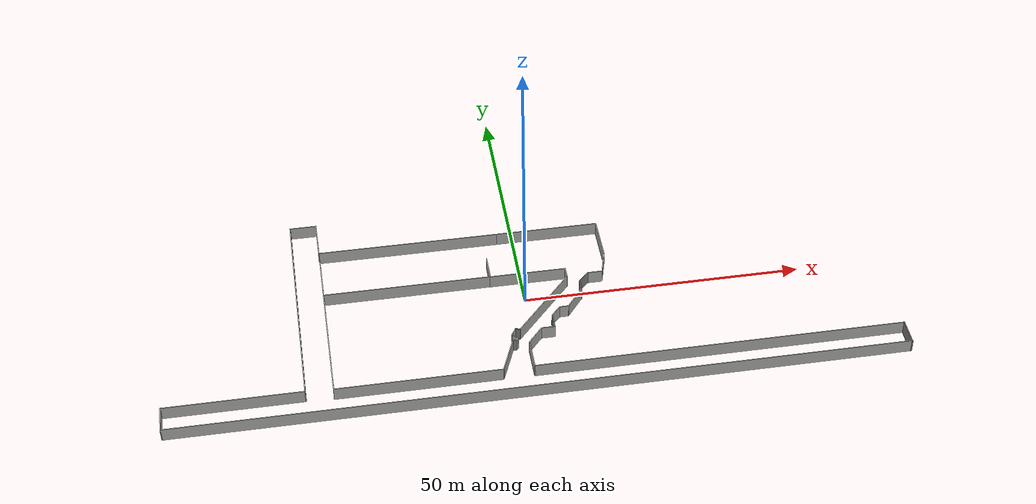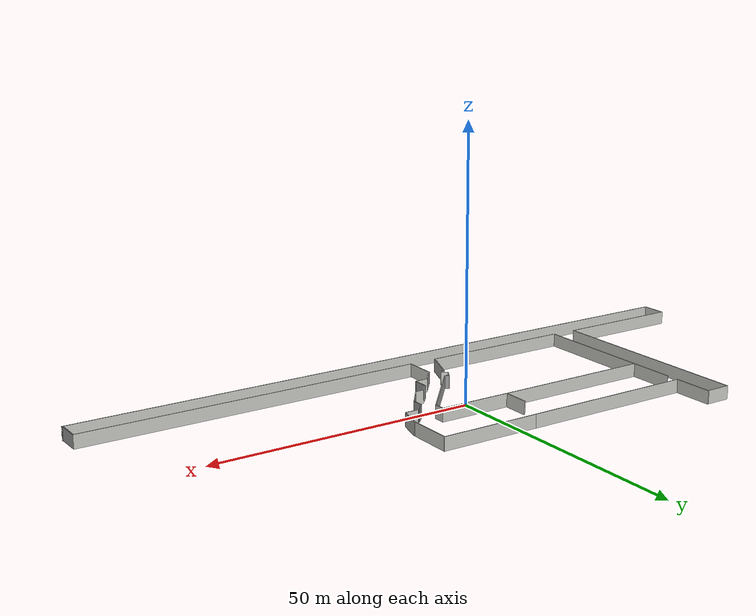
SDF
<?xml version='1.0'?>
<sdf version='1.7'>
  <model name='MIT_Tunnel_mod'>
    <link name='Wall_10'>
      <pose>-19.1952 15.5558 0 0 0 -0.001042</pose>
      <self_collide>0</self_collide>
      <enable_wind>0</enable_wind>
      <kinematic>0</kinematic>
      <visual name='Wall_10_Visual'>
        <pose>0 0 1.25 0 -0 0</pose>
        <geometry>
          <box>
            <size>32.6917 0.15 2.5</size>
          </box>
        </geometry>
        <material>
          <script>
            <uri>file://media/materials/scripts/gazebo.material</uri>
            <name>Gazebo/CeilingTiled</name>
          </script>
          <ambient>1 1 1 1</ambient>
          <shader type='pixel'/>
        </material>
        <transparency>0</transparency>
        <cast_shadows>1</cast_shadows>
      </visual>
      <collision name='Wall_10_Collision'>
        <laser_retro>0</laser_retro>
        <max_contacts>10</max_contacts>
        <pose>0 0 1.25 0 -0 0</pose>
        <geometry>
          <box>
            <size>32.6917 0.15 2.5</size>
          </box>
        </geometry>
        <surface>
          <friction>
            <ode>
              <mu>1</mu>
              <mu2>1</mu2>
              <fdir1>0 0 0</fdir1>
              <slip1>0</slip1>
              <slip2>0</slip2>
            </ode>
            <torsional>
              <coefficient>1</coefficient>
              <patch_radius>0</patch_radius>
              <surface_radius>0</surface_radius>
              <use_patch_radius>1</use_patch_radius>
              <ode>
                <slip>0</slip>
              </ode>
            </torsional>
          </friction>
          <bounce>
            <restitution_coefficient>0</restitution_coefficient>
            <threshold>1e+06</threshold>
          </bounce>
          <contact>
            <collide_without_contact>0</collide_without_contact>
            <collide_without_contact_bitmask>1</collide_without_contact_bitmask>
            <collide_bitmask>1</collide_bitmask>
            <ode>
              <soft_cfm>0</soft_cfm>
              <soft_erp>0.2</soft_erp>
              <kp>1e+13</kp>
              <kd>1</kd>
              <max_vel>0.01</max_vel>
              <min_depth>0</min_depth>
            </ode>
            <bullet>
              <split_impulse>1</split_impulse>
              <split_impulse_penetration_threshold>-0.01</split_impulse_penetration_threshold>
              <soft_cfm>0</soft_cfm>
              <soft_erp>0.2</soft_erp>
              <kp>1e+13</kp>
              <kd>1</kd>
            </bullet>
          </contact>
        </surface>
      </collision>
    </link>
    <link name='Wall_12'>
      <pose>15.6663 11.3569 0 0 0 -1.5708</pose>
      <self_collide>0</self_collide>
      <enable_wind>0</enable_wind>
      <kinematic>0</kinematic>
      <visual name='Wall_12_Visual'>
        <pose>0 0 1.25 0 -0 0</pose>
        <geometry>
          <box>
            <size>8.5 0.15 2.5</size>
          </box>
        </geometry>
        <material>
          <script>
            <uri>file://media/materials/scripts/gazebo.material</uri>
            <name>Gazebo/CeilingTiled</name>
          </script>
          <ambient>1 1 1 1</ambient>
          <shader type='pixel'/>
        </material>
        <transparency>0</transparency>
        <cast_shadows>1</cast_shadows>
      </visual>
      <collision name='Wall_12_Collision'>
        <laser_retro>0</laser_retro>
        <max_contacts>10</max_contacts>
        <pose>0 0 1.25 0 -0 0</pose>
        <geometry>
          <box>
            <size>8.5 0.15 2.5</size>
          </box>
        </geometry>
        <surface>
          <friction>
            <ode>
              <mu>1</mu>
              <mu2>1</mu2>
              <fdir1>0 0 0</fdir1>
              <slip1>0</slip1>
              <slip2>0</slip2>
            </ode>
            <torsional>
              <coefficient>1</coefficient>
              <patch_radius>0</patch_radius>
              <surface_radius>0</surface_radius>
              <use_patch_radius>1</use_patch_radius>
              <ode>
                <slip>0</slip>
              </ode>
            </torsional>
          </friction>
          <bounce>
            <restitution_coefficient>0</restitution_coefficient>
            <threshold>1e+06</threshold>
          </bounce>
          <contact>
            <collide_without_contact>0</collide_without_contact>
            <collide_without_contact_bitmask>1</collide_without_contact_bitmask>
            <collide_bitmask>1</collide_bitmask>
            <ode>
              <soft_cfm>0</soft_cfm>
              <soft_erp>0.2</soft_erp>
              <kp>1e+13</kp>
              <kd>1</kd>
              <max_vel>0.01</max_vel>
              <min_depth>0</min_depth>
            </ode>
            <bullet>
              <split_impulse>1</split_impulse>
              <split_impulse_penetration_threshold>-0.01</split_impulse_penetration_threshold>
              <soft_cfm>0</soft_cfm>
              <soft_erp>0.2</soft_erp>
              <kp>1e+13</kp>
              <kd>1</kd>
            </bullet>
          </contact>
        </surface>
      </collision>
    </link>
    <link name='Wall_15'>
      <pose>6.37605 15.5572 0 0 -0 0</pose>
      <self_collide>0</self_collide>
      <enable_wind>0</enable_wind>
      <kinematic>0</kinematic>
      <visual name='Wall_15_Visual'>
        <pose>0 0 1.25 0 -0 0</pose>
        <geometry>
          <box>
            <size>18.75 0.15 2.5</size>
          </box>
        </geometry>
        <material>
          <script>
            <uri>file://media/materials/scripts/gazebo.material</uri>
            <name>Gazebo/CeilingTiled</name>
          </script>
          <ambient>1 1 1 1</ambient>
          <shader type='pixel'/>
        </material>
        <transparency>0</transparency>
        <cast_shadows>1</cast_shadows>
      </visual>
      <collision name='Wall_15_Collision'>
        <laser_retro>0</laser_retro>
        <max_contacts>10</max_contacts>
        <pose>0 0 1.25 0 -0 0</pose>
        <geometry>
          <box>
            <size>18.75 0.15 2.5</size>
          </box>
        </geometry>
        <surface>
          <friction>
            <ode>
              <mu>1</mu>
              <mu2>1</mu2>
              <fdir1>0 0 0</fdir1>
              <slip1>0</slip1>
              <slip2>0</slip2>
            </ode>
            <torsional>
              <coefficient>1</coefficient>
              <patch_radius>0</patch_radius>
              <surface_radius>0</surface_radius>
              <use_patch_radius>1</use_patch_radius>
              <ode>
                <slip>0</slip>
              </ode>
            </torsional>
          </friction>
          <bounce>
            <restitution_coefficient>0</restitution_coefficient>
            <threshold>1e+06</threshold>
          </bounce>
          <contact>
            <collide_without_contact>0</collide_without_contact>
            <collide_without_contact_bitmask>1</collide_without_contact_bitmask>
            <collide_bitmask>1</collide_bitmask>
            <ode>
              <soft_cfm>0</soft_cfm>
              <soft_erp>0.2</soft_erp>
              <kp>1e+13</kp>
              <kd>1</kd>
              <max_vel>0.01</max_vel>
              <min_depth>0</min_depth>
            </ode>
            <bullet>
              <split_impulse>1</split_impulse>
              <split_impulse_penetration_threshold>-0.01</split_impulse_penetration_threshold>
              <soft_cfm>0</soft_cfm>
              <soft_erp>0.2</soft_erp>
              <kp>1e+13</kp>
              <kd>1</kd>
            </bullet>
          </contact>
        </surface>
      </collision>
    </link>
    <link name='Wall_17'>
      <pose>15.0799 4.96726 0 0 0 -1.8326</pose>
      <self_collide>0</self_collide>
      <enable_wind>0</enable_wind>
      <kinematic>0</kinematic>
      <visual name='Wall_17_Visual'>
        <pose>0 0 1.25 0 -0 0</pose>
        <geometry>
          <box>
            <size>4.75 0.15 2.5</size>
          </box>
        </geometry>
        <material>
          <script>
            <uri>file://media/materials/scripts/gazebo.material</uri>
            <name>Gazebo/CeilingTiled</name>
          </script>
          <ambient>1 1 1 1</ambient>
          <shader type='pixel'/>
        </material>
        <transparency>0</transparency>
        <cast_shadows>1</cast_shadows>
      </visual>
      <collision name='Wall_17_Collision'>
        <laser_retro>0</laser_retro>
        <max_contacts>10</max_contacts>
        <pose>0 0 1.25 0 -0 0</pose>
        <geometry>
          <box>
            <size>4.75 0.15 2.5</size>
          </box>
        </geometry>
        <surface>
          <friction>
            <ode>
              <mu>1</mu>
              <mu2>1</mu2>
              <fdir1>0 0 0</fdir1>
              <slip1>0</slip1>
              <slip2>0</slip2>
            </ode>
            <torsional>
              <coefficient>1</coefficient>
              <patch_radius>0</patch_radius>
              <surface_radius>0</surface_radius>
              <use_patch_radius>1</use_patch_radius>
              <ode>
                <slip>0</slip>
              </ode>
            </torsional>
          </friction>
          <bounce>
            <restitution_coefficient>0</restitution_coefficient>
            <threshold>1e+06</threshold>
          </bounce>
          <contact>
            <collide_without_contact>0</collide_without_contact>
            <collide_without_contact_bitmask>1</collide_without_contact_bitmask>
            <collide_bitmask>1</collide_bitmask>
            <ode>
              <soft_cfm>0</soft_cfm>
              <soft_erp>0.2</soft_erp>
              <kp>1e+13</kp>
              <kd>1</kd>
              <max_vel>0.01</max_vel>
              <min_depth>0</min_depth>
            </ode>
            <bullet>
              <split_impulse>1</split_impulse>
              <split_impulse_penetration_threshold>-0.01</split_impulse_penetration_threshold>
              <soft_cfm>0</soft_cfm>
              <soft_erp>0.2</soft_erp>
              <kp>1e+13</kp>
              <kd>1</kd>
            </bullet>
          </contact>
        </surface>
      </collision>
    </link>
    <link name='Wall_18'>
      <pose>13.1846 2.74563 0 0 -0 3.14159</pose>
      <self_collide>0</self_collide>
      <enable_wind>0</enable_wind>
      <kinematic>0</kinematic>
      <visual name='Wall_18_Visual'>
        <pose>0 0 1.25 0 -0 0</pose>
        <geometry>
          <box>
            <size>2.75 0.15 2.5</size>
          </box>
        </geometry>
        <material>
          <script>
            <uri>file://media/materials/scripts/gazebo.material</uri>
            <name>Gazebo/CeilingTiled</name>
          </script>
          <ambient>1 1 1 1</ambient>
          <shader type='pixel'/>
        </material>
        <transparency>0</transparency>
        <cast_shadows>1</cast_shadows>
      </visual>
      <collision name='Wall_18_Collision'>
        <laser_retro>0</laser_retro>
        <max_contacts>10</max_contacts>
        <pose>0 0 1.25 0 -0 0</pose>
        <geometry>
          <box>
            <size>2.75 0.15 2.5</size>
          </box>
        </geometry>
        <surface>
          <friction>
            <ode>
              <mu>1</mu>
              <mu2>1</mu2>
              <fdir1>0 0 0</fdir1>
              <slip1>0</slip1>
              <slip2>0</slip2>
            </ode>
            <torsional>
              <coefficient>1</coefficient>
              <patch_radius>0</patch_radius>
              <surface_radius>0</surface_radius>
              <use_patch_radius>1</use_patch_radius>
              <ode>
                <slip>0</slip>
              </ode>
            </torsional>
          </friction>
          <bounce>
            <restitution_coefficient>0</restitution_coefficient>
            <threshold>1e+06</threshold>
          </bounce>
          <contact>
            <collide_without_contact>0</collide_without_contact>
            <collide_without_contact_bitmask>1</collide_without_contact_bitmask>
            <collide_bitmask>1</collide_bitmask>
            <ode>
              <soft_cfm>0</soft_cfm>
              <soft_erp>0.2</soft_erp>
              <kp>1e+13</kp>
              <kd>1</kd>
              <max_vel>0.01</max_vel>
              <min_depth>0</min_depth>
            </ode>
            <bullet>
              <split_impulse>1</split_impulse>
              <split_impulse_penetration_threshold>-0.01</split_impulse_penetration_threshold>
              <soft_cfm>0</soft_cfm>
              <soft_erp>0.2</soft_erp>
              <kp>1e+13</kp>
              <kd>1</kd>
            </bullet>
          </contact>
        </surface>
      </collision>
    </link>
    <link name='Wall_19'>
      <pose>10.9654 1.82639 0 0 0 -2.35619</pose>
      <self_collide>0</self_collide>
      <enable_wind>0</enable_wind>
      <kinematic>0</kinematic>
      <visual name='Wall_19_Visual'>
        <pose>0 0 1.25 0 -0 0</pose>
        <geometry>
          <box>
            <size>2.75 0.15 2.5</size>
          </box>
        </geometry>
        <material>
          <script>
            <uri>file://media/materials/scripts/gazebo.material</uri>
            <name>Gazebo/Grey</name>
          </script>
          <ambient>1 1 1 1</ambient>
          <shader type='pixel'/>
        </material>
        <transparency>0</transparency>
        <cast_shadows>1</cast_shadows>
      </visual>
      <collision name='Wall_19_Collision'>
        <laser_retro>0</laser_retro>
        <max_contacts>10</max_contacts>
        <pose>0 0 1.25 0 -0 0</pose>
        <geometry>
          <box>
            <size>2.75 0.15 2.5</size>
          </box>
        </geometry>
        <surface>
          <friction>
            <ode>
              <mu>1</mu>
              <mu2>1</mu2>
              <fdir1>0 0 0</fdir1>
              <slip1>0</slip1>
              <slip2>0</slip2>
            </ode>
            <torsional>
              <coefficient>1</coefficient>
              <patch_radius>0</patch_radius>
              <surface_radius>0</surface_radius>
              <use_patch_radius>1</use_patch_radius>
              <ode>
                <slip>0</slip>
              </ode>
            </torsional>
          </friction>
          <bounce>
            <restitution_coefficient>0</restitution_coefficient>
            <threshold>1e+06</threshold>
          </bounce>
          <contact>
            <collide_without_contact>0</collide_without_contact>
            <collide_without_contact_bitmask>1</collide_without_contact_bitmask>
            <collide_bitmask>1</collide_bitmask>
            <ode>
              <soft_cfm>0</soft_cfm>
              <soft_erp>0.2</soft_erp>
              <kp>1e+13</kp>
              <kd>1</kd>
              <max_vel>0.01</max_vel>
              <min_depth>0</min_depth>
            </ode>
            <bullet>
              <split_impulse>1</split_impulse>
              <split_impulse_penetration_threshold>-0.01</split_impulse_penetration_threshold>
              <soft_cfm>0</soft_cfm>
              <soft_erp>0.2</soft_erp>
              <kp>1e+13</kp>
              <kd>1</kd>
            </bullet>
          </contact>
        </surface>
      </collision>
    </link>
    <link name='Wall_2'>
      <pose>-52.25 -18.2689 0 0 -0 0</pose>
      <self_collide>0</self_collide>
      <enable_wind>0</enable_wind>
      <kinematic>0</kinematic>
      <visual name='Wall_2_Visual'>
        <pose>0 0 1.25 0 -0 0</pose>
        <geometry>
          <box>
            <size>24.25 0.15 2.5</size>
          </box>
        </geometry>
        <material>
          <script>
            <uri>file://media/materials/scripts/gazebo.material</uri>
            <name>Gazebo/CeilingTiled</name>
          </script>
          <ambient>1 1 1 1</ambient>
          <shader type='pixel'/>
        </material>
        <transparency>0</transparency>
        <cast_shadows>1</cast_shadows>
      </visual>
      <collision name='Wall_2_Collision'>
        <laser_retro>0</laser_retro>
        <max_contacts>10</max_contacts>
        <pose>0 0 1.25 0 -0 0</pose>
        <geometry>
          <box>
            <size>24.25 0.15 2.5</size>
          </box>
        </geometry>
        <surface>
          <friction>
            <ode>
              <mu>1</mu>
              <mu2>1</mu2>
              <fdir1>0 0 0</fdir1>
              <slip1>0</slip1>
              <slip2>0</slip2>
            </ode>
            <torsional>
              <coefficient>1</coefficient>
              <patch_radius>0</patch_radius>
              <surface_radius>0</surface_radius>
              <use_patch_radius>1</use_patch_radius>
              <ode>
                <slip>0</slip>
              </ode>
            </torsional>
          </friction>
          <bounce>
            <restitution_coefficient>0</restitution_coefficient>
            <threshold>1e+06</threshold>
          </bounce>
          <contact>
            <collide_without_contact>0</collide_without_contact>
            <collide_without_contact_bitmask>1</collide_without_contact_bitmask>
            <collide_bitmask>1</collide_bitmask>
            <ode>
              <soft_cfm>0</soft_cfm>
              <soft_erp>0.2</soft_erp>
              <kp>1e+13</kp>
              <kd>1</kd>
              <max_vel>0.01</max_vel>
              <min_depth>0</min_depth>
            </ode>
            <bullet>
              <split_impulse>1</split_impulse>
              <split_impulse_penetration_threshold>-0.01</split_impulse_penetration_threshold>
              <soft_cfm>0</soft_cfm>
              <soft_erp>0.2</soft_erp>
              <kp>1e+13</kp>
              <kd>1</kd>
            </bullet>
          </contact>
        </surface>
      </collision>
    </link>
    <link name='Wall_20'>
      <pose>10.0461 -0.142849 0 0 0 -1.5708</pose>
      <self_collide>0</self_collide>
      <enable_wind>0</enable_wind>
      <kinematic>0</kinematic>
      <visual name='Wall_20_Visual'>
        <pose>0 0 1.25 0 -0 0</pose>
        <geometry>
          <box>
            <size>2.25 0.15 2.5</size>
          </box>
        </geometry>
        <material>
          <script>
            <uri>file://media/materials/scripts/gazebo.material</uri>
            <name>Gazebo/Grey</name>
          </script>
          <ambient>1 1 1 1</ambient>
          <shader type='pixel'/>
        </material>
        <transparency>0</transparency>
        <cast_shadows>1</cast_shadows>
      </visual>
      <collision name='Wall_20_Collision'>
        <laser_retro>0</laser_retro>
        <max_contacts>10</max_contacts>
        <pose>0 0 1.25 0 -0 0</pose>
        <geometry>
          <box>
            <size>2.25 0.15 2.5</size>
          </box>
        </geometry>
        <surface>
          <friction>
            <ode>
              <mu>1</mu>
              <mu2>1</mu2>
              <fdir1>0 0 0</fdir1>
              <slip1>0</slip1>
              <slip2>0</slip2>
            </ode>
            <torsional>
              <coefficient>1</coefficient>
              <patch_radius>0</patch_radius>
              <surface_radius>0</surface_radius>
              <use_patch_radius>1</use_patch_radius>
              <ode>
                <slip>0</slip>
              </ode>
            </torsional>
          </friction>
          <bounce>
            <restitution_coefficient>0</restitution_coefficient>
            <threshold>1e+06</threshold>
          </bounce>
          <contact>
            <collide_without_contact>0</collide_without_contact>
            <collide_without_contact_bitmask>1</collide_without_contact_bitmask>
            <collide_bitmask>1</collide_bitmask>
            <ode>
              <soft_cfm>0</soft_cfm>
              <soft_erp>0.2</soft_erp>
              <kp>1e+13</kp>
              <kd>1</kd>
              <max_vel>0.01</max_vel>
              <min_depth>0</min_depth>
            </ode>
            <bullet>
              <split_impulse>1</split_impulse>
              <split_impulse_penetration_threshold>-0.01</split_impulse_penetration_threshold>
              <soft_cfm>0</soft_cfm>
              <soft_erp>0.2</soft_erp>
              <kp>1e+13</kp>
              <kd>1</kd>
            </bullet>
          </contact>
        </surface>
      </collision>
    </link>
    <link name='Wall_22'>
      <pose>8.53852 -3.14869 0 0 0 -2.22749</pose>
      <self_collide>0</self_collide>
      <enable_wind>0</enable_wind>
      <kinematic>0</kinematic>
      <visual name='Wall_22_Visual'>
        <pose>0 0 1.25 0 -0 0</pose>
        <geometry>
          <box>
            <size>5.08891 0.15 2.5</size>
          </box>
        </geometry>
        <material>
          <script>
            <uri>file://media/materials/scripts/gazebo.material</uri>
            <name>Gazebo/CeilingTiled</name>
          </script>
          <ambient>1 1 1 1</ambient>
          <shader type='pixel'/>
        </material>
        <transparency>0</transparency>
        <cast_shadows>1</cast_shadows>
      </visual>
      <collision name='Wall_22_Collision'>
        <laser_retro>0</laser_retro>
        <max_contacts>10</max_contacts>
        <pose>0 0 1.25 0 -0 0</pose>
        <geometry>
          <box>
            <size>5.08891 0.15 2.5</size>
          </box>
        </geometry>
        <surface>
          <friction>
            <ode>
              <mu>1</mu>
              <mu2>1</mu2>
              <fdir1>0 0 0</fdir1>
              <slip1>0</slip1>
              <slip2>0</slip2>
            </ode>
            <torsional>
              <coefficient>1</coefficient>
              <patch_radius>0</patch_radius>
              <surface_radius>0</surface_radius>
              <use_patch_radius>1</use_patch_radius>
              <ode>
                <slip>0</slip>
              </ode>
            </torsional>
          </friction>
          <bounce>
            <restitution_coefficient>0</restitution_coefficient>
            <threshold>1e+06</threshold>
          </bounce>
          <contact>
            <collide_without_contact>0</collide_without_contact>
            <collide_without_contact_bitmask>1</collide_without_contact_bitmask>
            <collide_bitmask>1</collide_bitmask>
            <ode>
              <soft_cfm>0</soft_cfm>
              <soft_erp>0.2</soft_erp>
              <kp>1e+13</kp>
              <kd>1</kd>
              <max_vel>0.01</max_vel>
              <min_depth>0</min_depth>
            </ode>
            <bullet>
              <split_impulse>1</split_impulse>
              <split_impulse_penetration_threshold>-0.01</split_impulse_penetration_threshold>
              <soft_cfm>0</soft_cfm>
              <soft_erp>0.2</soft_erp>
              <kp>1e+13</kp>
              <kd>1</kd>
            </bullet>
          </contact>
        </surface>
      </collision>
    </link>
    <link name='Wall_23'>
      <pose>6.23091 -5.10454 0 0 -0 3.14159</pose>
      <self_collide>0</self_collide>
      <enable_wind>0</enable_wind>
      <kinematic>0</kinematic>
      <visual name='Wall_23_Visual'>
        <pose>0 0 1.25 0 -0 0</pose>
        <geometry>
          <box>
            <size>1.75 0.15 2.5</size>
          </box>
        </geometry>
        <material>
          <script>
            <uri>file://media/materials/scripts/gazebo.material</uri>
            <name>Gazebo/CeilingTiled</name>
          </script>
          <ambient>1 1 1 1</ambient>
          <shader type='pixel'/>
        </material>
        <transparency>0</transparency>
        <cast_shadows>1</cast_shadows>
      </visual>
      <collision name='Wall_23_Collision'>
        <laser_retro>0</laser_retro>
        <max_contacts>10</max_contacts>
        <pose>0 0 1.25 0 -0 0</pose>
        <geometry>
          <box>
            <size>1.75 0.15 2.5</size>
          </box>
        </geometry>
        <surface>
          <friction>
            <ode>
              <mu>1</mu>
              <mu2>1</mu2>
              <fdir1>0 0 0</fdir1>
              <slip1>0</slip1>
              <slip2>0</slip2>
            </ode>
            <torsional>
              <coefficient>1</coefficient>
              <patch_radius>0</patch_radius>
              <surface_radius>0</surface_radius>
              <use_patch_radius>1</use_patch_radius>
              <ode>
                <slip>0</slip>
              </ode>
            </torsional>
          </friction>
          <bounce>
            <restitution_coefficient>0</restitution_coefficient>
            <threshold>1e+06</threshold>
          </bounce>
          <contact>
            <collide_without_contact>0</collide_without_contact>
            <collide_without_contact_bitmask>1</collide_without_contact_bitmask>
            <collide_bitmask>1</collide_bitmask>
            <ode>
              <soft_cfm>0</soft_cfm>
              <soft_erp>0.2</soft_erp>
              <kp>1e+13</kp>
              <kd>1</kd>
              <max_vel>0.01</max_vel>
              <min_depth>0</min_depth>
            </ode>
            <bullet>
              <split_impulse>1</split_impulse>
              <split_impulse_penetration_threshold>-0.01</split_impulse_penetration_threshold>
              <soft_cfm>0</soft_cfm>
              <soft_erp>0.2</soft_erp>
              <kp>1e+13</kp>
              <kd>1</kd>
            </bullet>
          </contact>
        </surface>
      </collision>
    </link>
    <link name='Wall_24'>
      <pose>4.6163 -6.01417 0 0 0 -2.30114</pose>
      <self_collide>0</self_collide>
      <enable_wind>0</enable_wind>
      <kinematic>0</kinematic>
      <visual name='Wall_24_Visual'>
        <pose>0 0 1.25 0 -0 0</pose>
        <geometry>
          <box>
            <size>2.59216 0.15 2.5</size>
          </box>
        </geometry>
        <material>
          <script>
            <uri>file://media/materials/scripts/gazebo.material</uri>
            <name>Gazebo/CeilingTiled</name>
          </script>
          <ambient>1 1 1 1</ambient>
          <shader type='pixel'/>
        </material>
        <transparency>0</transparency>
        <cast_shadows>1</cast_shadows>
      </visual>
      <collision name='Wall_24_Collision'>
        <laser_retro>0</laser_retro>
        <max_contacts>10</max_contacts>
        <pose>0 0 1.25 0 -0 0</pose>
        <geometry>
          <box>
            <size>2.59216 0.15 2.5</size>
          </box>
        </geometry>
        <surface>
          <friction>
            <ode>
              <mu>1</mu>
              <mu2>1</mu2>
              <fdir1>0 0 0</fdir1>
              <slip1>0</slip1>
              <slip2>0</slip2>
            </ode>
            <torsional>
              <coefficient>1</coefficient>
              <patch_radius>0</patch_radius>
              <surface_radius>0</surface_radius>
              <use_patch_radius>1</use_patch_radius>
              <ode>
                <slip>0</slip>
              </ode>
            </torsional>
          </friction>
          <bounce>
            <restitution_coefficient>0</restitution_coefficient>
            <threshold>1e+06</threshold>
          </bounce>
          <contact>
            <collide_without_contact>0</collide_without_contact>
            <collide_without_contact_bitmask>1</collide_without_contact_bitmask>
            <collide_bitmask>1</collide_bitmask>
            <ode>
              <soft_cfm>0</soft_cfm>
              <soft_erp>0.2</soft_erp>
              <kp>1e+13</kp>
              <kd>1</kd>
              <max_vel>0.01</max_vel>
              <min_depth>0</min_depth>
            </ode>
            <bullet>
              <split_impulse>1</split_impulse>
              <split_impulse_penetration_threshold>-0.01</split_impulse_penetration_threshold>
              <soft_cfm>0</soft_cfm>
              <soft_erp>0.2</soft_erp>
              <kp>1e+13</kp>
              <kd>1</kd>
            </bullet>
          </contact>
        </surface>
      </collision>
    </link>
    <link name='Wall_26'>
      <pose>3.80168 -8.34882 0 0 0 -1.5708</pose>
      <self_collide>0</self_collide>
      <enable_wind>0</enable_wind>
      <kinematic>0</kinematic>
      <visual name='Wall_26_Visual'>
        <pose>0 0 1.25 0 -0 0</pose>
        <geometry>
          <box>
            <size>3 0.15 2.5</size>
          </box>
        </geometry>
        <material>
          <script>
            <uri>file://media/materials/scripts/gazebo.material</uri>
            <name>Gazebo/Grey</name>
          </script>
          <ambient>1 1 1 1</ambient>
          <shader type='pixel'/>
        </material>
        <transparency>0</transparency>
        <cast_shadows>1</cast_shadows>
      </visual>
      <collision name='Wall_26_Collision'>
        <laser_retro>0</laser_retro>
        <max_contacts>10</max_contacts>
        <pose>0 0 1.25 0 -0 0</pose>
        <geometry>
          <box>
            <size>3 0.15 2.5</size>
          </box>
        </geometry>
        <surface>
          <friction>
            <ode>
              <mu>1</mu>
              <mu2>1</mu2>
              <fdir1>0 0 0</fdir1>
              <slip1>0</slip1>
              <slip2>0</slip2>
            </ode>
            <torsional>
              <coefficient>1</coefficient>
              <patch_radius>0</patch_radius>
              <surface_radius>0</surface_radius>
              <use_patch_radius>1</use_patch_radius>
              <ode>
                <slip>0</slip>
              </ode>
            </torsional>
          </friction>
          <bounce>
            <restitution_coefficient>0</restitution_coefficient>
            <threshold>1e+06</threshold>
          </bounce>
          <contact>
            <collide_without_contact>0</collide_without_contact>
            <collide_without_contact_bitmask>1</collide_without_contact_bitmask>
            <collide_bitmask>1</collide_bitmask>
            <ode>
              <soft_cfm>0</soft_cfm>
              <soft_erp>0.2</soft_erp>
              <kp>1e+13</kp>
              <kd>1</kd>
              <max_vel>0.01</max_vel>
              <min_depth>0</min_depth>
            </ode>
            <bullet>
              <split_impulse>1</split_impulse>
              <split_impulse_penetration_threshold>-0.01</split_impulse_penetration_threshold>
              <soft_cfm>0</soft_cfm>
              <soft_erp>0.2</soft_erp>
              <kp>1e+13</kp>
              <kd>1</kd>
            </bullet>
          </contact>
        </surface>
      </collision>
    </link>
    <link name='Wall_27'>
      <pose>2.62668 -9.77382 0 0 -0 3.14159</pose>
      <self_collide>0</self_collide>
      <enable_wind>0</enable_wind>
      <kinematic>0</kinematic>
      <visual name='Wall_27_Visual'>
        <pose>0 0 1.25 0 -0 0</pose>
        <geometry>
          <box>
            <size>2.5 0.15 2.5</size>
          </box>
        </geometry>
        <material>
          <script>
            <uri>file://media/materials/scripts/gazebo.material</uri>
            <name>Gazebo/CeilingTiled</name>
          </script>
          <ambient>1 1 1 1</ambient>
          <shader type='pixel'/>
        </material>
        <transparency>0</transparency>
        <cast_shadows>1</cast_shadows>
      </visual>
      <collision name='Wall_27_Collision'>
        <laser_retro>0</laser_retro>
        <max_contacts>10</max_contacts>
        <pose>0 0 1.25 0 -0 0</pose>
        <geometry>
          <box>
            <size>2.5 0.15 2.5</size>
          </box>
        </geometry>
        <surface>
          <friction>
            <ode>
              <mu>1</mu>
              <mu2>1</mu2>
              <fdir1>0 0 0</fdir1>
              <slip1>0</slip1>
              <slip2>0</slip2>
            </ode>
            <torsional>
              <coefficient>1</coefficient>
              <patch_radius>0</patch_radius>
              <surface_radius>0</surface_radius>
              <use_patch_radius>1</use_patch_radius>
              <ode>
                <slip>0</slip>
              </ode>
            </torsional>
          </friction>
          <bounce>
            <restitution_coefficient>0</restitution_coefficient>
            <threshold>1e+06</threshold>
          </bounce>
          <contact>
            <collide_without_contact>0</collide_without_contact>
            <collide_without_contact_bitmask>1</collide_without_contact_bitmask>
            <collide_bitmask>1</collide_bitmask>
            <ode>
              <soft_cfm>0</soft_cfm>
              <soft_erp>0.2</soft_erp>
              <kp>1e+13</kp>
              <kd>1</kd>
              <max_vel>0.01</max_vel>
              <min_depth>0</min_depth>
            </ode>
            <bullet>
              <split_impulse>1</split_impulse>
              <split_impulse_penetration_threshold>-0.01</split_impulse_penetration_threshold>
              <soft_cfm>0</soft_cfm>
              <soft_erp>0.2</soft_erp>
              <kp>1e+13</kp>
              <kd>1</kd>
            </bullet>
          </contact>
        </surface>
      </collision>
    </link>
    <link name='Wall_28'>
      <pose>0.152007 -11.2946 0 0 0 -2.27796</pose>
      <self_collide>0</self_collide>
      <enable_wind>0</enable_wind>
      <kinematic>0</kinematic>
      <visual name='Wall_28_Visual'>
        <pose>0 0 1.25 0 -0 0</pose>
        <geometry>
          <box>
            <size>4.15096 0.15 2.5</size>
          </box>
        </geometry>
        <material>
          <script>
            <uri>file://media/materials/scripts/gazebo.material</uri>
            <name>Gazebo/CeilingTiled</name>
          </script>
          <ambient>1 1 1 1</ambient>
          <shader type='pixel'/>
        </material>
        <transparency>0</transparency>
        <cast_shadows>1</cast_shadows>
      </visual>
      <collision name='Wall_28_Collision'>
        <laser_retro>0</laser_retro>
        <max_contacts>10</max_contacts>
        <pose>0 0 1.25 0 -0 0</pose>
        <geometry>
          <box>
            <size>4.15096 0.15 2.5</size>
          </box>
        </geometry>
        <surface>
          <friction>
            <ode>
              <mu>1</mu>
              <mu2>1</mu2>
              <fdir1>0 0 0</fdir1>
              <slip1>0</slip1>
              <slip2>0</slip2>
            </ode>
            <torsional>
              <coefficient>1</coefficient>
              <patch_radius>0</patch_radius>
              <surface_radius>0</surface_radius>
              <use_patch_radius>1</use_patch_radius>
              <ode>
                <slip>0</slip>
              </ode>
            </torsional>
          </friction>
          <bounce>
            <restitution_coefficient>0</restitution_coefficient>
            <threshold>1e+06</threshold>
          </bounce>
          <contact>
            <collide_without_contact>0</collide_without_contact>
            <collide_without_contact_bitmask>1</collide_without_contact_bitmask>
            <collide_bitmask>1</collide_bitmask>
            <ode>
              <soft_cfm>0</soft_cfm>
              <soft_erp>0.2</soft_erp>
              <kp>1e+13</kp>
              <kd>1</kd>
              <max_vel>0.01</max_vel>
              <min_depth>0</min_depth>
            </ode>
            <bullet>
              <split_impulse>1</split_impulse>
              <split_impulse_penetration_threshold>-0.01</split_impulse_penetration_threshold>
              <soft_cfm>0</soft_cfm>
              <soft_erp>0.2</soft_erp>
              <kp>1e+13</kp>
              <kd>1</kd>
            </bullet>
          </contact>
        </surface>
      </collision>
    </link>
    <link name='Wall_29'>
      <pose>-1.14312 -15.679 0 0 0 -1.56921</pose>
      <self_collide>0</self_collide>
      <enable_wind>0</enable_wind>
      <kinematic>0</kinematic>
      <visual name='Wall_29_Visual'>
        <pose>0 0 1.25 0 -0 0</pose>
        <geometry>
          <box>
            <size>5.87777 0.15 2.5</size>
          </box>
        </geometry>
        <material>
          <script>
            <uri>file://media/materials/scripts/gazebo.material</uri>
            <name>Gazebo/CeilingTiled</name>
          </script>
          <ambient>1 1 1 1</ambient>
          <shader type='pixel'/>
        </material>
        <transparency>0</transparency>
        <cast_shadows>1</cast_shadows>
      </visual>
      <collision name='Wall_29_Collision'>
        <laser_retro>0</laser_retro>
        <max_contacts>10</max_contacts>
        <pose>0 0 1.25 0 -0 0</pose>
        <geometry>
          <box>
            <size>5.87777 0.15 2.5</size>
          </box>
        </geometry>
        <surface>
          <friction>
            <ode>
              <mu>1</mu>
              <mu2>1</mu2>
              <fdir1>0 0 0</fdir1>
              <slip1>0</slip1>
              <slip2>0</slip2>
            </ode>
            <torsional>
              <coefficient>1</coefficient>
              <patch_radius>0</patch_radius>
              <surface_radius>0</surface_radius>
              <use_patch_radius>1</use_patch_radius>
              <ode>
                <slip>0</slip>
              </ode>
            </torsional>
          </friction>
          <bounce>
            <restitution_coefficient>0</restitution_coefficient>
            <threshold>1e+06</threshold>
          </bounce>
          <contact>
            <collide_without_contact>0</collide_without_contact>
            <collide_without_contact_bitmask>1</collide_without_contact_bitmask>
            <collide_bitmask>1</collide_bitmask>
            <ode>
              <soft_cfm>0</soft_cfm>
              <soft_erp>0.2</soft_erp>
              <kp>1e+13</kp>
              <kd>1</kd>
              <max_vel>0.01</max_vel>
              <min_depth>0</min_depth>
            </ode>
            <bullet>
              <split_impulse>1</split_impulse>
              <split_impulse_penetration_threshold>-0.01</split_impulse_penetration_threshold>
              <soft_cfm>0</soft_cfm>
              <soft_erp>0.2</soft_erp>
              <kp>1e+13</kp>
              <kd>1</kd>
            </bullet>
          </contact>
        </surface>
      </collision>
    </link>
    <link name='Wall_30'>
      <pose>31.5103 -18.5427 0 0 -0 0</pose>
      <self_collide>0</self_collide>
      <enable_wind>0</enable_wind>
      <kinematic>0</kinematic>
      <visual name='Wall_30_Visual'>
        <pose>0 0 1.25 0 -0 0</pose>
        <geometry>
          <box>
            <size>65.5 0.15 2.5</size>
          </box>
        </geometry>
        <material>
          <script>
            <uri>file://media/materials/scripts/gazebo.material</uri>
            <name>Gazebo/CeilingTiled</name>
          </script>
          <ambient>1 1 1 1</ambient>
          <shader type='pixel'/>
        </material>
        <transparency>0</transparency>
        <cast_shadows>1</cast_shadows>
      </visual>
      <collision name='Wall_30_Collision'>
        <laser_retro>0</laser_retro>
        <max_contacts>10</max_contacts>
        <pose>0 0 1.25 0 -0 0</pose>
        <geometry>
          <box>
            <size>65.5 0.15 2.5</size>
          </box>
        </geometry>
        <surface>
          <friction>
            <ode>
              <mu>1</mu>
              <mu2>1</mu2>
              <fdir1>0 0 0</fdir1>
              <slip1>0</slip1>
              <slip2>0</slip2>
            </ode>
            <torsional>
              <coefficient>1</coefficient>
              <patch_radius>0</patch_radius>
              <surface_radius>0</surface_radius>
              <use_patch_radius>1</use_patch_radius>
              <ode>
                <slip>0</slip>
              </ode>
            </torsional>
          </friction>
          <bounce>
            <restitution_coefficient>0</restitution_coefficient>
            <threshold>1e+06</threshold>
          </bounce>
          <contact>
            <collide_without_contact>0</collide_without_contact>
            <collide_without_contact_bitmask>1</collide_without_contact_bitmask>
            <collide_bitmask>1</collide_bitmask>
            <ode>
              <soft_cfm>0</soft_cfm>
              <soft_erp>0.2</soft_erp>
              <kp>1e+13</kp>
              <kd>1</kd>
              <max_vel>0.01</max_vel>
              <min_depth>0</min_depth>
            </ode>
            <bullet>
              <split_impulse>1</split_impulse>
              <split_impulse_penetration_threshold>-0.01</split_impulse_penetration_threshold>
              <soft_cfm>0</soft_cfm>
              <soft_erp>0.2</soft_erp>
              <kp>1e+13</kp>
              <kd>1</kd>
            </bullet>
          </contact>
        </surface>
      </collision>
    </link>
    <link name='Wall_32'>
      <pose>64.1853 -20.8427 0 0 0 -1.5708</pose>
      <self_collide>0</self_collide>
      <enable_wind>0</enable_wind>
      <kinematic>0</kinematic>
      <visual name='Wall_32_Visual'>
        <pose>0 0 1.25 0 -0 0</pose>
        <geometry>
          <box>
            <size>4.75 0.15 2.5</size>
          </box>
        </geometry>
        <material>
          <script>
            <uri>file://media/materials/scripts/gazebo.material</uri>
            <name>Gazebo/Grey</name>
          </script>
          <ambient>1 1 1 1</ambient>
          <shader type='pixel'/>
        </material>
        <transparency>0</transparency>
        <cast_shadows>1</cast_shadows>
      </visual>
      <collision name='Wall_32_Collision'>
        <laser_retro>0</laser_retro>
        <max_contacts>10</max_contacts>
        <pose>0 0 1.25 0 -0 0</pose>
        <geometry>
          <box>
            <size>4.75 0.15 2.5</size>
          </box>
        </geometry>
        <surface>
          <friction>
            <ode>
              <mu>1</mu>
              <mu2>1</mu2>
              <fdir1>0 0 0</fdir1>
              <slip1>0</slip1>
              <slip2>0</slip2>
            </ode>
            <torsional>
              <coefficient>1</coefficient>
              <patch_radius>0</patch_radius>
              <surface_radius>0</surface_radius>
              <use_patch_radius>1</use_patch_radius>
              <ode>
                <slip>0</slip>
              </ode>
            </torsional>
          </friction>
          <bounce>
            <restitution_coefficient>0</restitution_coefficient>
            <threshold>1e+06</threshold>
          </bounce>
          <contact>
            <collide_without_contact>0</collide_without_contact>
            <collide_without_contact_bitmask>1</collide_without_contact_bitmask>
            <collide_bitmask>1</collide_bitmask>
            <ode>
              <soft_cfm>0</soft_cfm>
              <soft_erp>0.2</soft_erp>
              <kp>1e+13</kp>
              <kd>1</kd>
              <max_vel>0.01</max_vel>
              <min_depth>0</min_depth>
            </ode>
            <bullet>
              <split_impulse>1</split_impulse>
              <split_impulse_penetration_threshold>-0.01</split_impulse_penetration_threshold>
              <soft_cfm>0</soft_cfm>
              <soft_erp>0.2</soft_erp>
              <kp>1e+13</kp>
              <kd>1</kd>
            </bullet>
          </contact>
        </surface>
      </collision>
    </link>
    <link name='Wall_34'>
      <pose>-64.3 -20.6939 0 0 0 -1.5708</pose>
      <self_collide>0</self_collide>
      <enable_wind>0</enable_wind>
      <kinematic>0</kinematic>
      <visual name='Wall_34_Visual'>
        <pose>0 0 1.25 0 -0 0</pose>
        <geometry>
          <box>
            <size>5 0.15 2.5</size>
          </box>
        </geometry>
        <material>
          <script>
            <uri>file://media/materials/scripts/gazebo.material</uri>
            <name>Gazebo/CeilingTiled</name>
          </script>
          <ambient>1 1 1 1</ambient>
          <shader type='pixel'/>
        </material>
        <transparency>0</transparency>
        <cast_shadows>1</cast_shadows>
      </visual>
      <collision name='Wall_34_Collision'>
        <laser_retro>0</laser_retro>
        <max_contacts>10</max_contacts>
        <pose>0 0 1.25 0 -0 0</pose>
        <geometry>
          <box>
            <size>5 0.15 2.5</size>
          </box>
        </geometry>
        <surface>
          <friction>
            <ode>
              <mu>1</mu>
              <mu2>1</mu2>
              <fdir1>0 0 0</fdir1>
              <slip1>0</slip1>
              <slip2>0</slip2>
            </ode>
            <torsional>
              <coefficient>1</coefficient>
              <patch_radius>0</patch_radius>
              <surface_radius>0</surface_radius>
              <use_patch_radius>1</use_patch_radius>
              <ode>
                <slip>0</slip>
              </ode>
            </torsional>
          </friction>
          <bounce>
            <restitution_coefficient>0</restitution_coefficient>
            <threshold>1e+06</threshold>
          </bounce>
          <contact>
            <collide_without_contact>0</collide_without_contact>
            <collide_without_contact_bitmask>1</collide_without_contact_bitmask>
            <collide_bitmask>1</collide_bitmask>
            <ode>
              <soft_cfm>0</soft_cfm>
              <soft_erp>0.2</soft_erp>
              <kp>1e+13</kp>
              <kd>1</kd>
              <max_vel>0.01</max_vel>
              <min_depth>0</min_depth>
            </ode>
            <bullet>
              <split_impulse>1</split_impulse>
              <split_impulse_penetration_threshold>-0.01</split_impulse_penetration_threshold>
              <soft_cfm>0</soft_cfm>
              <soft_erp>0.2</soft_erp>
              <kp>1e+13</kp>
              <kd>1</kd>
            </bullet>
          </contact>
        </surface>
      </collision>
    </link>
    <link name='Wall_35'>
      <pose>1e-06 -23.1189 0 0 -0 0</pose>
      <self_collide>0</self_collide>
      <enable_wind>0</enable_wind>
      <kinematic>0</kinematic>
      <visual name='Wall_35_Visual'>
        <pose>0 0 1.25 0 -0 0</pose>
        <geometry>
          <box>
            <size>128.75 0.15 2.5</size>
          </box>
        </geometry>
        <material>
          <script>
            <uri>file://media/materials/scripts/gazebo.material</uri>
            <name>Gazebo/CeilingTiled</name>
          </script>
          <ambient>1 1 1 1</ambient>
          <shader type='pixel'/>
        </material>
        <transparency>0</transparency>
        <cast_shadows>1</cast_shadows>
      </visual>
      <collision name='Wall_35_Collision'>
        <laser_retro>0</laser_retro>
        <max_contacts>10</max_contacts>
        <pose>0 0 1.25 0 -0 0</pose>
        <geometry>
          <box>
            <size>128.75 0.15 2.5</size>
          </box>
        </geometry>
        <surface>
          <friction>
            <ode>
              <mu>1</mu>
              <mu2>1</mu2>
              <fdir1>0 0 0</fdir1>
              <slip1>0</slip1>
              <slip2>0</slip2>
            </ode>
            <torsional>
              <coefficient>1</coefficient>
              <patch_radius>0</patch_radius>
              <surface_radius>0</surface_radius>
              <use_patch_radius>1</use_patch_radius>
              <ode>
                <slip>0</slip>
              </ode>
            </torsional>
          </friction>
          <bounce>
            <restitution_coefficient>0</restitution_coefficient>
            <threshold>1e+06</threshold>
          </bounce>
          <contact>
            <collide_without_contact>0</collide_without_contact>
            <collide_without_contact_bitmask>1</collide_without_contact_bitmask>
            <collide_bitmask>1</collide_bitmask>
            <ode>
              <soft_cfm>0</soft_cfm>
              <soft_erp>0.2</soft_erp>
              <kp>1e+13</kp>
              <kd>1</kd>
              <max_vel>0.01</max_vel>
              <min_depth>0</min_depth>
            </ode>
            <bullet>
              <split_impulse>1</split_impulse>
              <split_impulse_penetration_threshold>-0.01</split_impulse_penetration_threshold>
              <soft_cfm>0</soft_cfm>
              <soft_erp>0.2</soft_erp>
              <kp>1e+13</kp>
              <kd>1</kd>
            </bullet>
          </contact>
        </surface>
      </collision>
    </link>
    <link name='Wall_37'>
      <pose>-37.9 23.0811 0 0 -0 0</pose>
      <self_collide>0</self_collide>
      <enable_wind>0</enable_wind>
      <kinematic>0</kinematic>
      <visual name='Wall_37_Visual'>
        <pose>0 0 1.25 0 -0 0</pose>
        <geometry>
          <box>
            <size>4.75 0.15 2.5</size>
          </box>
        </geometry>
        <material>
          <script>
            <uri>file://media/materials/scripts/gazebo.material</uri>
            <name>Gazebo/CeilingTiled</name>
          </script>
          <ambient>1 1 1 1</ambient>
          <shader type='pixel'/>
        </material>
        <transparency>0</transparency>
        <cast_shadows>1</cast_shadows>
      </visual>
      <collision name='Wall_37_Collision'>
        <laser_retro>0</laser_retro>
        <max_contacts>10</max_contacts>
        <pose>0 0 1.25 0 -0 0</pose>
        <geometry>
          <box>
            <size>4.75 0.15 2.5</size>
          </box>
        </geometry>
        <surface>
          <friction>
            <ode>
              <mu>1</mu>
              <mu2>1</mu2>
              <fdir1>0 0 0</fdir1>
              <slip1>0</slip1>
              <slip2>0</slip2>
            </ode>
            <torsional>
              <coefficient>1</coefficient>
              <patch_radius>0</patch_radius>
              <surface_radius>0</surface_radius>
              <use_patch_radius>1</use_patch_radius>
              <ode>
                <slip>0</slip>
              </ode>
            </torsional>
          </friction>
          <bounce>
            <restitution_coefficient>0</restitution_coefficient>
            <threshold>1e+06</threshold>
          </bounce>
          <contact>
            <collide_without_contact>0</collide_without_contact>
            <collide_without_contact_bitmask>1</collide_without_contact_bitmask>
            <collide_bitmask>1</collide_bitmask>
            <ode>
              <soft_cfm>0</soft_cfm>
              <soft_erp>0.2</soft_erp>
              <kp>1e+13</kp>
              <kd>1</kd>
              <max_vel>0.01</max_vel>
              <min_depth>0</min_depth>
            </ode>
            <bullet>
              <split_impulse>1</split_impulse>
              <split_impulse_penetration_threshold>-0.01</split_impulse_penetration_threshold>
              <soft_cfm>0</soft_cfm>
              <soft_erp>0.2</soft_erp>
              <kp>1e+13</kp>
              <kd>1</kd>
            </bullet>
          </contact>
        </surface>
      </collision>
    </link>
    <link name='Wall_41'>
      <pose>-35.4175 -2.72616 0 0 -0 1.5708</pose>
      <self_collide>0</self_collide>
      <enable_wind>0</enable_wind>
      <kinematic>0</kinematic>
      <visual name='Wall_41_Visual'>
        <pose>0 0 1.25 0 -0 0</pose>
        <geometry>
          <box>
            <size>31.75 0.15 2.5</size>
          </box>
        </geometry>
        <material>
          <script>
            <uri>file://media/materials/scripts/gazebo.material</uri>
            <name>Gazebo/CeilingTiled</name>
          </script>
          <ambient>1 1 1 1</ambient>
          <shader type='pixel'/>
        </material>
        <transparency>0</transparency>
        <cast_shadows>1</cast_shadows>
      </visual>
      <collision name='Wall_41_Collision'>
        <laser_retro>0</laser_retro>
        <max_contacts>10</max_contacts>
        <pose>0 0 1.25 0 -0 0</pose>
        <geometry>
          <box>
            <size>31.75 0.15 2.5</size>
          </box>
        </geometry>
        <surface>
          <friction>
            <ode>
              <mu>1</mu>
              <mu2>1</mu2>
              <fdir1>0 0 0</fdir1>
              <slip1>0</slip1>
              <slip2>0</slip2>
            </ode>
            <torsional>
              <coefficient>1</coefficient>
              <patch_radius>0</patch_radius>
              <surface_radius>0</surface_radius>
              <use_patch_radius>1</use_patch_radius>
              <ode>
                <slip>0</slip>
              </ode>
            </torsional>
          </friction>
          <bounce>
            <restitution_coefficient>0</restitution_coefficient>
            <threshold>1e+06</threshold>
          </bounce>
          <contact>
            <collide_without_contact>0</collide_without_contact>
            <collide_without_contact_bitmask>1</collide_without_contact_bitmask>
            <collide_bitmask>1</collide_bitmask>
            <ode>
              <soft_cfm>0</soft_cfm>
              <soft_erp>0.2</soft_erp>
              <kp>1e+13</kp>
              <kd>1</kd>
              <max_vel>0.01</max_vel>
              <min_depth>0</min_depth>
            </ode>
            <bullet>
              <split_impulse>1</split_impulse>
              <split_impulse_penetration_threshold>-0.01</split_impulse_penetration_threshold>
              <soft_cfm>0</soft_cfm>
              <soft_erp>0.2</soft_erp>
              <kp>1e+13</kp>
              <kd>1</kd>
            </bullet>
          </contact>
        </surface>
      </collision>
    </link>
    <link name='Wall_43'>
      <pose>-20.4925 4.50154 0 0 -0 0</pose>
      <self_collide>0</self_collide>
      <enable_wind>0</enable_wind>
      <kinematic>0</kinematic>
      <visual name='Wall_43_Visual'>
        <pose>0 0 1.25 0 -0 0</pose>
        <geometry>
          <box>
            <size>30 0.15 2.5</size>
          </box>
        </geometry>
        <material>
          <script>
            <uri>file://media/materials/scripts/gazebo.material</uri>
            <name>Gazebo/CeilingTiled</name>
          </script>
          <ambient>1 1 1 1</ambient>
          <shader type='pixel'/>
        </material>
        <transparency>0</transparency>
        <cast_shadows>1</cast_shadows>
      </visual>
      <collision name='Wall_43_Collision'>
        <laser_retro>0</laser_retro>
        <max_contacts>10</max_contacts>
        <pose>0 0 1.25 0 -0 0</pose>
        <geometry>
          <box>
            <size>30 0.15 2.5</size>
          </box>
        </geometry>
        <surface>
          <friction>
            <ode>
              <mu>1</mu>
              <mu2>1</mu2>
              <fdir1>0 0 0</fdir1>
              <slip1>0</slip1>
              <slip2>0</slip2>
            </ode>
            <torsional>
              <coefficient>1</coefficient>
              <patch_radius>0</patch_radius>
              <surface_radius>0</surface_radius>
              <use_patch_radius>1</use_patch_radius>
              <ode>
                <slip>0</slip>
              </ode>
            </torsional>
          </friction>
          <bounce>
            <restitution_coefficient>0</restitution_coefficient>
            <threshold>1e+06</threshold>
          </bounce>
          <contact>
            <collide_without_contact>0</collide_without_contact>
            <collide_without_contact_bitmask>1</collide_without_contact_bitmask>
            <collide_bitmask>1</collide_bitmask>
            <ode>
              <soft_cfm>0</soft_cfm>
              <soft_erp>0.2</soft_erp>
              <kp>1e+13</kp>
              <kd>1</kd>
              <max_vel>0.01</max_vel>
              <min_depth>0</min_depth>
            </ode>
            <bullet>
              <split_impulse>1</split_impulse>
              <split_impulse_penetration_threshold>-0.01</split_impulse_penetration_threshold>
              <soft_cfm>0</soft_cfm>
              <soft_erp>0.2</soft_erp>
              <kp>1e+13</kp>
              <kd>1</kd>
            </bullet>
          </contact>
        </surface>
      </collision>
    </link>
    <link name='Wall_44'>
      <pose>-5.56746 6.92907 0 0 0 -1.5708</pose>
      <self_collide>0</self_collide>
      <enable_wind>0</enable_wind>
      <kinematic>0</kinematic>
      <gravity>1</gravity>
      <inertial>
        <mass>1</mass>
        <pose>0 0 0 0 -0 0</pose>
        <inertia>
          <ixx>1</ixx>
          <ixy>0</ixy>
          <ixz>0</ixz>
          <iyy>1</iyy>
          <iyz>0</iyz>
          <izz>1</izz>
        </inertia>
      </inertial>
      <visual name='Wall_44_Visual'>
        <pose>0 0 1.25 0 -0 0</pose>
        <geometry>
          <box>
            <size>5 0.15 2.5</size>
          </box>
        </geometry>
        <material>
          <script>
            <uri>file://media/materials/scripts/gazebo.material</uri>
            <name>Gazebo/CeilingTiled</name>
          </script>
          <ambient>1 1 1 1</ambient>
          <shader type='pixel'>
            <normal_map>__default__</normal_map>
          </shader>
          <diffuse>1 1 1 1</diffuse>
          <specular>0 0 0 1</specular>
          <emissive>0 0 0 1</emissive>
        </material>
        <transparency>0</transparency>
        <cast_shadows>1</cast_shadows>
      </visual>
      <collision name='Wall_44_Collision'>
        <laser_retro>0</laser_retro>
        <max_contacts>10</max_contacts>
        <pose>0 0 1.25 0 -0 0</pose>
        <geometry>
          <box>
            <size>5 0.15 2.5</size>
          </box>
        </geometry>
        <surface>
          <friction>
            <ode>
              <mu>1</mu>
              <mu2>1</mu2>
              <fdir1>0 0 0</fdir1>
              <slip1>0</slip1>
              <slip2>0</slip2>
            </ode>
            <torsional>
              <coefficient>1</coefficient>
              <patch_radius>0</patch_radius>
              <surface_radius>0</surface_radius>
              <use_patch_radius>1</use_patch_radius>
              <ode>
                <slip>0</slip>
              </ode>
            </torsional>
          </friction>
          <bounce>
            <restitution_coefficient>0</restitution_coefficient>
            <threshold>1e+06</threshold>
          </bounce>
          <contact>
            <collide_without_contact>0</collide_without_contact>
            <collide_without_contact_bitmask>1</collide_without_contact_bitmask>
            <collide_bitmask>1</collide_bitmask>
            <ode>
              <soft_cfm>0</soft_cfm>
              <soft_erp>0.2</soft_erp>
              <kp>1e+13</kp>
              <kd>1</kd>
              <max_vel>0.01</max_vel>
              <min_depth>0</min_depth>
            </ode>
            <bullet>
              <split_impulse>1</split_impulse>
              <split_impulse_penetration_threshold>-0.01</split_impulse_penetration_threshold>
              <soft_cfm>0</soft_cfm>
              <soft_erp>0.2</soft_erp>
              <kp>1e+13</kp>
              <kd>1</kd>
            </bullet>
          </contact>
        </surface>
      </collision>
    </link>
    <link name='Wall_45'>
      <pose>1.23255 4.47384 0 0 -0 0</pose>
      <self_collide>0</self_collide>
      <enable_wind>0</enable_wind>
      <kinematic>0</kinematic>
      <visual name='Wall_45_Visual'>
        <pose>0 0 1.25 0 -0 0</pose>
        <geometry>
          <box>
            <size>13.75 0.15 2.5</size>
          </box>
        </geometry>
        <material>
          <script>
            <uri>file://media/materials/scripts/gazebo.material</uri>
            <name>Gazebo/CeilingTiled</name>
          </script>
          <ambient>1 1 1 1</ambient>
          <shader type='pixel'/>
        </material>
        <transparency>0</transparency>
        <cast_shadows>1</cast_shadows>
      </visual>
      <collision name='Wall_45_Collision'>
        <laser_retro>0</laser_retro>
        <max_contacts>10</max_contacts>
        <pose>0 0 1.25 0 -0 0</pose>
        <geometry>
          <box>
            <size>13.75 0.15 2.5</size>
          </box>
        </geometry>
        <surface>
          <friction>
            <ode>
              <mu>1</mu>
              <mu2>1</mu2>
              <fdir1>0 0 0</fdir1>
              <slip1>0</slip1>
              <slip2>0</slip2>
            </ode>
            <torsional>
              <coefficient>1</coefficient>
              <patch_radius>0</patch_radius>
              <surface_radius>0</surface_radius>
              <use_patch_radius>1</use_patch_radius>
              <ode>
                <slip>0</slip>
              </ode>
            </torsional>
          </friction>
          <bounce>
            <restitution_coefficient>0</restitution_coefficient>
            <threshold>1e+06</threshold>
          </bounce>
          <contact>
            <collide_without_contact>0</collide_without_contact>
            <collide_without_contact_bitmask>1</collide_without_contact_bitmask>
            <collide_bitmask>1</collide_bitmask>
            <ode>
              <soft_cfm>0</soft_cfm>
              <soft_erp>0.2</soft_erp>
              <kp>1e+13</kp>
              <kd>1</kd>
              <max_vel>0.01</max_vel>
              <min_depth>0</min_depth>
            </ode>
            <bullet>
              <split_impulse>1</split_impulse>
              <split_impulse_penetration_threshold>-0.01</split_impulse_penetration_threshold>
              <soft_cfm>0</soft_cfm>
              <soft_erp>0.2</soft_erp>
              <kp>1e+13</kp>
              <kd>1</kd>
            </bullet>
          </contact>
        </surface>
      </collision>
    </link>
    <link name='Wall_46'>
      <pose>8.03255 3.42384 0 0 0 -1.5708</pose>
      <self_collide>0</self_collide>
      <enable_wind>0</enable_wind>
      <kinematic>0</kinematic>
      <visual name='Wall_46_Visual'>
        <pose>0 0 1.25 0 -0 0</pose>
        <geometry>
          <box>
            <size>2.25 0.15 2.5</size>
          </box>
        </geometry>
        <material>
          <script>
            <uri>file://media/materials/scripts/gazebo.material</uri>
            <name>Gazebo/CeilingTiled</name>
          </script>
          <ambient>1 1 1 1</ambient>
          <shader type='pixel'/>
        </material>
        <transparency>0</transparency>
        <cast_shadows>1</cast_shadows>
      </visual>
      <collision name='Wall_46_Collision'>
        <laser_retro>0</laser_retro>
        <max_contacts>10</max_contacts>
        <pose>0 0 1.25 0 -0 0</pose>
        <geometry>
          <box>
            <size>2.25 0.15 2.5</size>
          </box>
        </geometry>
        <surface>
          <friction>
            <ode>
              <mu>1</mu>
              <mu2>1</mu2>
              <fdir1>0 0 0</fdir1>
              <slip1>0</slip1>
              <slip2>0</slip2>
            </ode>
            <torsional>
              <coefficient>1</coefficient>
              <patch_radius>0</patch_radius>
              <surface_radius>0</surface_radius>
              <use_patch_radius>1</use_patch_radius>
              <ode>
                <slip>0</slip>
              </ode>
            </torsional>
          </friction>
          <bounce>
            <restitution_coefficient>0</restitution_coefficient>
            <threshold>1e+06</threshold>
          </bounce>
          <contact>
            <collide_without_contact>0</collide_without_contact>
            <collide_without_contact_bitmask>1</collide_without_contact_bitmask>
            <collide_bitmask>1</collide_bitmask>
            <ode>
              <soft_cfm>0</soft_cfm>
              <soft_erp>0.2</soft_erp>
              <kp>1e+13</kp>
              <kd>1</kd>
              <max_vel>0.01</max_vel>
              <min_depth>0</min_depth>
            </ode>
            <bullet>
              <split_impulse>1</split_impulse>
              <split_impulse_penetration_threshold>-0.01</split_impulse_penetration_threshold>
              <soft_cfm>0</soft_cfm>
              <soft_erp>0.2</soft_erp>
              <kp>1e+13</kp>
              <kd>1</kd>
            </bullet>
          </contact>
        </surface>
      </collision>
    </link>
    <link name='Wall_47'>
      <pose>2.89068 -3.54071 0 0 0 -2.28642</pose>
      <self_collide>0</self_collide>
      <enable_wind>0</enable_wind>
      <kinematic>0</kinematic>
      <visual name='Wall_47_Visual'>
        <pose>0 0 1.25 0 -0 0</pose>
        <geometry>
          <box>
            <size>15.8243 0.15 2.5</size>
          </box>
        </geometry>
        <material>
          <script>
            <uri>file://media/materials/scripts/gazebo.material</uri>
            <name>Gazebo/CeilingTiled</name>
          </script>
          <ambient>1 1 1 1</ambient>
          <shader type='pixel'/>
        </material>
        <transparency>0</transparency>
        <cast_shadows>1</cast_shadows>
      </visual>
      <collision name='Wall_47_Collision'>
        <laser_retro>0</laser_retro>
        <max_contacts>10</max_contacts>
        <pose>0 0 1.25 0 -0 0</pose>
        <geometry>
          <box>
            <size>15.8243 0.15 2.5</size>
          </box>
        </geometry>
        <surface>
          <friction>
            <ode>
              <mu>1</mu>
              <mu2>1</mu2>
              <fdir1>0 0 0</fdir1>
              <slip1>0</slip1>
              <slip2>0</slip2>
            </ode>
            <torsional>
              <coefficient>1</coefficient>
              <patch_radius>0</patch_radius>
              <surface_radius>0</surface_radius>
              <use_patch_radius>1</use_patch_radius>
              <ode>
                <slip>0</slip>
              </ode>
            </torsional>
          </friction>
          <bounce>
            <restitution_coefficient>0</restitution_coefficient>
            <threshold>1e+06</threshold>
          </bounce>
          <contact>
            <collide_without_contact>0</collide_without_contact>
            <collide_without_contact_bitmask>1</collide_without_contact_bitmask>
            <collide_bitmask>1</collide_bitmask>
            <ode>
              <soft_cfm>0</soft_cfm>
              <soft_erp>0.2</soft_erp>
              <kp>1e+13</kp>
              <kd>1</kd>
              <max_vel>0.01</max_vel>
              <min_depth>0</min_depth>
            </ode>
            <bullet>
              <split_impulse>1</split_impulse>
              <split_impulse_penetration_threshold>-0.01</split_impulse_penetration_threshold>
              <soft_cfm>0</soft_cfm>
              <soft_erp>0.2</soft_erp>
              <kp>1e+13</kp>
              <kd>1</kd>
            </bullet>
          </contact>
        </surface>
      </collision>
    </link>
    <link name='Wall_5'>
      <pose>-40.2 2.40609 0 0 -0 1.5708</pose>
      <self_collide>0</self_collide>
      <enable_wind>0</enable_wind>
      <kinematic>0</kinematic>
      <visual name='Wall_5_Visual'>
        <pose>0 0 1.25 0 -0 0</pose>
        <geometry>
          <box>
            <size>41.5 0.15 2.5</size>
          </box>
        </geometry>
        <material>
          <script>
            <uri>file://media/materials/scripts/gazebo.material</uri>
            <name>Gazebo/CeilingTiled</name>
          </script>
          <ambient>1 1 1 1</ambient>
          <shader type='pixel'/>
        </material>
        <transparency>0</transparency>
        <cast_shadows>1</cast_shadows>
      </visual>
      <collision name='Wall_5_Collision'>
        <laser_retro>0</laser_retro>
        <max_contacts>10</max_contacts>
        <pose>0 0 1.25 0 -0 0</pose>
        <geometry>
          <box>
            <size>41.5 0.15 2.5</size>
          </box>
        </geometry>
        <surface>
          <friction>
            <ode>
              <mu>1</mu>
              <mu2>1</mu2>
              <fdir1>0 0 0</fdir1>
              <slip1>0</slip1>
              <slip2>0</slip2>
            </ode>
            <torsional>
              <coefficient>1</coefficient>
              <patch_radius>0</patch_radius>
              <surface_radius>0</surface_radius>
              <use_patch_radius>1</use_patch_radius>
              <ode>
                <slip>0</slip>
              </ode>
            </torsional>
          </friction>
          <bounce>
            <restitution_coefficient>0</restitution_coefficient>
            <threshold>1e+06</threshold>
          </bounce>
          <contact>
            <collide_without_contact>0</collide_without_contact>
            <collide_without_contact_bitmask>1</collide_without_contact_bitmask>
            <collide_bitmask>1</collide_bitmask>
            <ode>
              <soft_cfm>0</soft_cfm>
              <soft_erp>0.2</soft_erp>
              <kp>1e+13</kp>
              <kd>1</kd>
              <max_vel>0.01</max_vel>
              <min_depth>0</min_depth>
            </ode>
            <bullet>
              <split_impulse>1</split_impulse>
              <split_impulse_penetration_threshold>-0.01</split_impulse_penetration_threshold>
              <soft_cfm>0</soft_cfm>
              <soft_erp>0.2</soft_erp>
              <kp>1e+13</kp>
              <kd>1</kd>
            </bullet>
          </contact>
        </surface>
      </collision>
    </link>
    <link name='Wall_50'>
      <pose>-2.6617 -9.34526 0 0 -0 2.87979</pose>
      <self_collide>0</self_collide>
      <enable_wind>0</enable_wind>
      <kinematic>0</kinematic>
      <visual name='Wall_50_Visual'>
        <pose>0 0 1.25 0 -0 0</pose>
        <geometry>
          <box>
            <size>1 0.15 2.5</size>
          </box>
        </geometry>
        <material>
          <script>
            <uri>file://media/materials/scripts/gazebo.material</uri>
            <name>Gazebo/Grey</name>
          </script>
          <ambient>1 1 1 1</ambient>
          <shader type='pixel'/>
        </material>
        <transparency>0</transparency>
        <cast_shadows>1</cast_shadows>
      </visual>
      <collision name='Wall_50_Collision'>
        <laser_retro>0</laser_retro>
        <max_contacts>10</max_contacts>
        <pose>0 0 1.25 0 -0 0</pose>
        <geometry>
          <box>
            <size>1 0.15 2.5</size>
          </box>
        </geometry>
        <surface>
          <friction>
            <ode>
              <mu>1</mu>
              <mu2>1</mu2>
              <fdir1>0 0 0</fdir1>
              <slip1>0</slip1>
              <slip2>0</slip2>
            </ode>
            <torsional>
              <coefficient>1</coefficient>
              <patch_radius>0</patch_radius>
              <surface_radius>0</surface_radius>
              <use_patch_radius>1</use_patch_radius>
              <ode>
                <slip>0</slip>
              </ode>
            </torsional>
          </friction>
          <bounce>
            <restitution_coefficient>0</restitution_coefficient>
            <threshold>1e+06</threshold>
          </bounce>
          <contact>
            <collide_without_contact>0</collide_without_contact>
            <collide_without_contact_bitmask>1</collide_without_contact_bitmask>
            <collide_bitmask>1</collide_bitmask>
            <ode>
              <soft_cfm>0</soft_cfm>
              <soft_erp>0.2</soft_erp>
              <kp>1e+13</kp>
              <kd>1</kd>
              <max_vel>0.01</max_vel>
              <min_depth>0</min_depth>
            </ode>
            <bullet>
              <split_impulse>1</split_impulse>
              <split_impulse_penetration_threshold>-0.01</split_impulse_penetration_threshold>
              <soft_cfm>0</soft_cfm>
              <soft_erp>0.2</soft_erp>
              <kp>1e+13</kp>
              <kd>1</kd>
            </bullet>
          </contact>
        </surface>
      </collision>
    </link>
    <link name='Wall_51'>
      <pose>-3.47221 -9.92808 0 0 0 -2.0944</pose>
      <self_collide>0</self_collide>
      <enable_wind>0</enable_wind>
      <kinematic>0</kinematic>
      <visual name='Wall_51_Visual'>
        <pose>0 0 1.25 0 -0 0</pose>
        <geometry>
          <box>
            <size>1.75 0.15 2.5</size>
          </box>
        </geometry>
        <material>
          <script>
            <uri>file://media/materials/scripts/gazebo.material</uri>
            <name>Gazebo/CeilingTiled</name>
          </script>
          <ambient>1 1 1 1</ambient>
          <shader type='pixel'/>
        </material>
        <transparency>0</transparency>
        <cast_shadows>1</cast_shadows>
      </visual>
      <collision name='Wall_51_Collision'>
        <laser_retro>0</laser_retro>
        <max_contacts>10</max_contacts>
        <pose>0 0 1.25 0 -0 0</pose>
        <geometry>
          <box>
            <size>1.75 0.15 2.5</size>
          </box>
        </geometry>
        <surface>
          <friction>
            <ode>
              <mu>1</mu>
              <mu2>1</mu2>
              <fdir1>0 0 0</fdir1>
              <slip1>0</slip1>
              <slip2>0</slip2>
            </ode>
            <torsional>
              <coefficient>1</coefficient>
              <patch_radius>0</patch_radius>
              <surface_radius>0</surface_radius>
              <use_patch_radius>1</use_patch_radius>
              <ode>
                <slip>0</slip>
              </ode>
            </torsional>
          </friction>
          <bounce>
            <restitution_coefficient>0</restitution_coefficient>
            <threshold>1e+06</threshold>
          </bounce>
          <contact>
            <collide_without_contact>0</collide_without_contact>
            <collide_without_contact_bitmask>1</collide_without_contact_bitmask>
            <collide_bitmask>1</collide_bitmask>
            <ode>
              <soft_cfm>0</soft_cfm>
              <soft_erp>0.2</soft_erp>
              <kp>1e+13</kp>
              <kd>1</kd>
              <max_vel>0.01</max_vel>
              <min_depth>0</min_depth>
            </ode>
            <bullet>
              <split_impulse>1</split_impulse>
              <split_impulse_penetration_threshold>-0.01</split_impulse_penetration_threshold>
              <soft_cfm>0</soft_cfm>
              <soft_erp>0.2</soft_erp>
              <kp>1e+13</kp>
              <kd>1</kd>
            </bullet>
          </contact>
        </surface>
      </collision>
    </link>
    <link name='Wall_52'>
      <pose>-3.39492 -11.0982 0 0 0 -0.785398</pose>
      <self_collide>0</self_collide>
      <enable_wind>0</enable_wind>
      <kinematic>0</kinematic>
      <visual name='Wall_52_Visual'>
        <pose>0 0 1.25 0 -0 0</pose>
        <geometry>
          <box>
            <size>1.5 0.15 2.5</size>
          </box>
        </geometry>
        <material>
          <script>
            <uri>file://media/materials/scripts/gazebo.material</uri>
            <name>Gazebo/CeilingTiled</name>
          </script>
          <ambient>1 1 1 1</ambient>
          <shader type='pixel'/>
        </material>
        <transparency>0</transparency>
        <cast_shadows>1</cast_shadows>
      </visual>
      <collision name='Wall_52_Collision'>
        <laser_retro>0</laser_retro>
        <max_contacts>10</max_contacts>
        <pose>0 0 1.25 0 -0 0</pose>
        <geometry>
          <box>
            <size>1.5 0.15 2.5</size>
          </box>
        </geometry>
        <surface>
          <friction>
            <ode>
              <mu>1</mu>
              <mu2>1</mu2>
              <fdir1>0 0 0</fdir1>
              <slip1>0</slip1>
              <slip2>0</slip2>
            </ode>
            <torsional>
              <coefficient>1</coefficient>
              <patch_radius>0</patch_radius>
              <surface_radius>0</surface_radius>
              <use_patch_radius>1</use_patch_radius>
              <ode>
                <slip>0</slip>
              </ode>
            </torsional>
          </friction>
          <bounce>
            <restitution_coefficient>0</restitution_coefficient>
            <threshold>1e+06</threshold>
          </bounce>
          <contact>
            <collide_without_contact>0</collide_without_contact>
            <collide_without_contact_bitmask>1</collide_without_contact_bitmask>
            <collide_bitmask>1</collide_bitmask>
            <ode>
              <soft_cfm>0</soft_cfm>
              <soft_erp>0.2</soft_erp>
              <kp>1e+13</kp>
              <kd>1</kd>
              <max_vel>0.01</max_vel>
              <min_depth>0</min_depth>
            </ode>
            <bullet>
              <split_impulse>1</split_impulse>
              <split_impulse_penetration_threshold>-0.01</split_impulse_penetration_threshold>
              <soft_cfm>0</soft_cfm>
              <soft_erp>0.2</soft_erp>
              <kp>1e+13</kp>
              <kd>1</kd>
            </bullet>
          </contact>
        </surface>
      </collision>
    </link>
    <link name='Wall_53'>
      <pose>-3.12975 -11.7876 0 0 0 -2.35619</pose>
      <self_collide>0</self_collide>
      <enable_wind>0</enable_wind>
      <kinematic>0</kinematic>
      <visual name='Wall_53_Visual'>
        <pose>0 0 1.25 0 -0 0</pose>
        <geometry>
          <box>
            <size>0.75 0.15 2.5</size>
          </box>
        </geometry>
        <material>
          <script>
            <uri>file://media/materials/scripts/gazebo.material</uri>
            <name>Gazebo/CeilingTiled</name>
          </script>
          <ambient>1 1 1 1</ambient>
          <shader type='pixel'/>
        </material>
        <transparency>0</transparency>
        <cast_shadows>1</cast_shadows>
      </visual>
      <collision name='Wall_53_Collision'>
        <laser_retro>0</laser_retro>
        <max_contacts>10</max_contacts>
        <pose>0 0 1.25 0 -0 0</pose>
        <geometry>
          <box>
            <size>0.75 0.15 2.5</size>
          </box>
        </geometry>
        <surface>
          <friction>
            <ode>
              <mu>1</mu>
              <mu2>1</mu2>
              <fdir1>0 0 0</fdir1>
              <slip1>0</slip1>
              <slip2>0</slip2>
            </ode>
            <torsional>
              <coefficient>1</coefficient>
              <patch_radius>0</patch_radius>
              <surface_radius>0</surface_radius>
              <use_patch_radius>1</use_patch_radius>
              <ode>
                <slip>0</slip>
              </ode>
            </torsional>
          </friction>
          <bounce>
            <restitution_coefficient>0</restitution_coefficient>
            <threshold>1e+06</threshold>
          </bounce>
          <contact>
            <collide_without_contact>0</collide_without_contact>
            <collide_without_contact_bitmask>1</collide_without_contact_bitmask>
            <collide_bitmask>1</collide_bitmask>
            <ode>
              <soft_cfm>0</soft_cfm>
              <soft_erp>0.2</soft_erp>
              <kp>1e+13</kp>
              <kd>1</kd>
              <max_vel>0.01</max_vel>
              <min_depth>0</min_depth>
            </ode>
            <bullet>
              <split_impulse>1</split_impulse>
              <split_impulse_penetration_threshold>-0.01</split_impulse_penetration_threshold>
              <soft_cfm>0</soft_cfm>
              <soft_erp>0.2</soft_erp>
              <kp>1e+13</kp>
              <kd>1</kd>
            </bullet>
          </contact>
        </surface>
      </collision>
    </link>
    <link name='Wall_54'>
      <pose>-3.64188 -11.9998 0 0 -0 3.14159</pose>
      <self_collide>0</self_collide>
      <enable_wind>0</enable_wind>
      <kinematic>0</kinematic>
      <visual name='Wall_54_Visual'>
        <pose>0 0 1.25 0 -0 0</pose>
        <geometry>
          <box>
            <size>0.75 0.15 2.5</size>
          </box>
        </geometry>
        <material>
          <script>
            <uri>file://media/materials/scripts/gazebo.material</uri>
            <name>Gazebo/Grey</name>
          </script>
          <ambient>1 1 1 1</ambient>
          <shader type='pixel'/>
        </material>
        <transparency>0</transparency>
        <cast_shadows>1</cast_shadows>
      </visual>
      <collision name='Wall_54_Collision'>
        <laser_retro>0</laser_retro>
        <max_contacts>10</max_contacts>
        <pose>0 0 1.25 0 -0 0</pose>
        <geometry>
          <box>
            <size>0.75 0.15 2.5</size>
          </box>
        </geometry>
        <surface>
          <friction>
            <ode>
              <mu>1</mu>
              <mu2>1</mu2>
              <fdir1>0 0 0</fdir1>
              <slip1>0</slip1>
              <slip2>0</slip2>
            </ode>
            <torsional>
              <coefficient>1</coefficient>
              <patch_radius>0</patch_radius>
              <surface_radius>0</surface_radius>
              <use_patch_radius>1</use_patch_radius>
              <ode>
                <slip>0</slip>
              </ode>
            </torsional>
          </friction>
          <bounce>
            <restitution_coefficient>0</restitution_coefficient>
            <threshold>1e+06</threshold>
          </bounce>
          <contact>
            <collide_without_contact>0</collide_without_contact>
            <collide_without_contact_bitmask>1</collide_without_contact_bitmask>
            <collide_bitmask>1</collide_bitmask>
            <ode>
              <soft_cfm>0</soft_cfm>
              <soft_erp>0.2</soft_erp>
              <kp>1e+13</kp>
              <kd>1</kd>
              <max_vel>0.01</max_vel>
              <min_depth>0</min_depth>
            </ode>
            <bullet>
              <split_impulse>1</split_impulse>
              <split_impulse_penetration_threshold>-0.01</split_impulse_penetration_threshold>
              <soft_cfm>0</soft_cfm>
              <soft_erp>0.2</soft_erp>
              <kp>1e+13</kp>
              <kd>1</kd>
            </bullet>
          </contact>
        </surface>
      </collision>
    </link>
    <link name='Wall_55'>
      <pose>-5.21192 -15.2524 0 0 0 -1.94306</pose>
      <self_collide>0</self_collide>
      <enable_wind>0</enable_wind>
      <kinematic>0</kinematic>
      <visual name='Wall_55_Visual'>
        <pose>0 0 1.25 0 -0 0</pose>
        <geometry>
          <box>
            <size>7.13355 0.15 2.5</size>
          </box>
        </geometry>
        <material>
          <script>
            <uri>file://media/materials/scripts/gazebo.material</uri>
            <name>Gazebo/CeilingTiled</name>
          </script>
          <ambient>1 1 1 1</ambient>
          <shader type='pixel'/>
        </material>
        <transparency>0</transparency>
        <cast_shadows>1</cast_shadows>
      </visual>
      <collision name='Wall_55_Collision'>
        <laser_retro>0</laser_retro>
        <max_contacts>10</max_contacts>
        <pose>0 0 1.25 0 -0 0</pose>
        <geometry>
          <box>
            <size>7.13355 0.15 2.5</size>
          </box>
        </geometry>
        <surface>
          <friction>
            <ode>
              <mu>1</mu>
              <mu2>1</mu2>
              <fdir1>0 0 0</fdir1>
              <slip1>0</slip1>
              <slip2>0</slip2>
            </ode>
            <torsional>
              <coefficient>1</coefficient>
              <patch_radius>0</patch_radius>
              <surface_radius>0</surface_radius>
              <use_patch_radius>1</use_patch_radius>
              <ode>
                <slip>0</slip>
              </ode>
            </torsional>
          </friction>
          <bounce>
            <restitution_coefficient>0</restitution_coefficient>
            <threshold>1e+06</threshold>
          </bounce>
          <contact>
            <collide_without_contact>0</collide_without_contact>
            <collide_without_contact_bitmask>1</collide_without_contact_bitmask>
            <collide_bitmask>1</collide_bitmask>
            <ode>
              <soft_cfm>0</soft_cfm>
              <soft_erp>0.2</soft_erp>
              <kp>1e+13</kp>
              <kd>1</kd>
              <max_vel>0.01</max_vel>
              <min_depth>0</min_depth>
            </ode>
            <bullet>
              <split_impulse>1</split_impulse>
              <split_impulse_penetration_threshold>-0.01</split_impulse_penetration_threshold>
              <soft_cfm>0</soft_cfm>
              <soft_erp>0.2</soft_erp>
              <kp>1e+13</kp>
              <kd>1</kd>
            </bullet>
          </contact>
        </surface>
      </collision>
    </link>
    <link name='Wall_57'>
      <pose>-20.9925 -18.5262 0 0 -0 0</pose>
      <self_collide>0</self_collide>
      <enable_wind>0</enable_wind>
      <kinematic>0</kinematic>
      <visual name='Wall_57_Visual'>
        <pose>0 0 1.25 0 -0 0</pose>
        <geometry>
          <box>
            <size>29 0.15 2.5</size>
          </box>
        </geometry>
        <material>
          <script>
            <uri>file://media/materials/scripts/gazebo.material</uri>
            <name>Gazebo/CeilingTiled</name>
          </script>
          <ambient>1 1 1 1</ambient>
          <shader type='pixel'/>
        </material>
        <transparency>0</transparency>
        <cast_shadows>1</cast_shadows>
      </visual>
      <collision name='Wall_57_Collision'>
        <laser_retro>0</laser_retro>
        <max_contacts>10</max_contacts>
        <pose>0 0 1.25 0 -0 0</pose>
        <geometry>
          <box>
            <size>29 0.15 2.5</size>
          </box>
        </geometry>
        <surface>
          <friction>
            <ode>
              <mu>1</mu>
              <mu2>1</mu2>
              <fdir1>0 0 0</fdir1>
              <slip1>0</slip1>
              <slip2>0</slip2>
            </ode>
            <torsional>
              <coefficient>1</coefficient>
              <patch_radius>0</patch_radius>
              <surface_radius>0</surface_radius>
              <use_patch_radius>1</use_patch_radius>
              <ode>
                <slip>0</slip>
              </ode>
            </torsional>
          </friction>
          <bounce>
            <restitution_coefficient>0</restitution_coefficient>
            <threshold>1e+06</threshold>
          </bounce>
          <contact>
            <collide_without_contact>0</collide_without_contact>
            <collide_without_contact_bitmask>1</collide_without_contact_bitmask>
            <collide_bitmask>1</collide_bitmask>
            <ode>
              <soft_cfm>0</soft_cfm>
              <soft_erp>0.2</soft_erp>
              <kp>1e+13</kp>
              <kd>1</kd>
              <max_vel>0.01</max_vel>
              <min_depth>0</min_depth>
            </ode>
            <bullet>
              <split_impulse>1</split_impulse>
              <split_impulse_penetration_threshold>-0.01</split_impulse_penetration_threshold>
              <soft_cfm>0</soft_cfm>
              <soft_erp>0.2</soft_erp>
              <kp>1e+13</kp>
              <kd>1</kd>
            </bullet>
          </contact>
        </surface>
      </collision>
    </link>
    <link name='Wall_9'>
      <pose>-35.4657 19.3427 0 0 0 -1.5708</pose>
      <self_collide>0</self_collide>
      <enable_wind>0</enable_wind>
      <kinematic>0</kinematic>
      <visual name='Wall_9_Visual'>
        <pose>0 0 1.25 0 -0 0</pose>
        <geometry>
          <box>
            <size>7.75 0.15 2.5</size>
          </box>
        </geometry>
        <material>
          <script>
            <uri>file://media/materials/scripts/gazebo.material</uri>
            <name>Gazebo/CeilingTiled</name>
          </script>
          <ambient>1 1 1 1</ambient>
          <shader type='pixel'/>
        </material>
        <transparency>0</transparency>
        <cast_shadows>1</cast_shadows>
      </visual>
      <collision name='Wall_9_Collision'>
        <laser_retro>0</laser_retro>
        <max_contacts>10</max_contacts>
        <pose>0 0 1.25 0 -0 0</pose>
        <geometry>
          <box>
            <size>7.75 0.15 2.5</size>
          </box>
        </geometry>
        <surface>
          <friction>
            <ode>
              <mu>1</mu>
              <mu2>1</mu2>
              <fdir1>0 0 0</fdir1>
              <slip1>0</slip1>
              <slip2>0</slip2>
            </ode>
            <torsional>
              <coefficient>1</coefficient>
              <patch_radius>0</patch_radius>
              <surface_radius>0</surface_radius>
              <use_patch_radius>1</use_patch_radius>
              <ode>
                <slip>0</slip>
              </ode>
            </torsional>
          </friction>
          <bounce>
            <restitution_coefficient>0</restitution_coefficient>
            <threshold>1e+06</threshold>
          </bounce>
          <contact>
            <collide_without_contact>0</collide_without_contact>
            <collide_without_contact_bitmask>1</collide_without_contact_bitmask>
            <collide_bitmask>1</collide_bitmask>
            <ode>
              <soft_cfm>0</soft_cfm>
              <soft_erp>0.2</soft_erp>
              <kp>1e+13</kp>
              <kd>1</kd>
              <max_vel>0.01</max_vel>
              <min_depth>0</min_depth>
            </ode>
            <bullet>
              <split_impulse>1</split_impulse>
              <split_impulse_penetration_threshold>-0.01</split_impulse_penetration_threshold>
              <soft_cfm>0</soft_cfm>
              <soft_erp>0.2</soft_erp>
              <kp>1e+13</kp>
              <kd>1</kd>
            </bullet>
          </contact>
        </surface>
      </collision>
    </link>
    <static>1</static>
    <allow_auto_disable>1</allow_auto_disable>
  </model>
</sdf>
